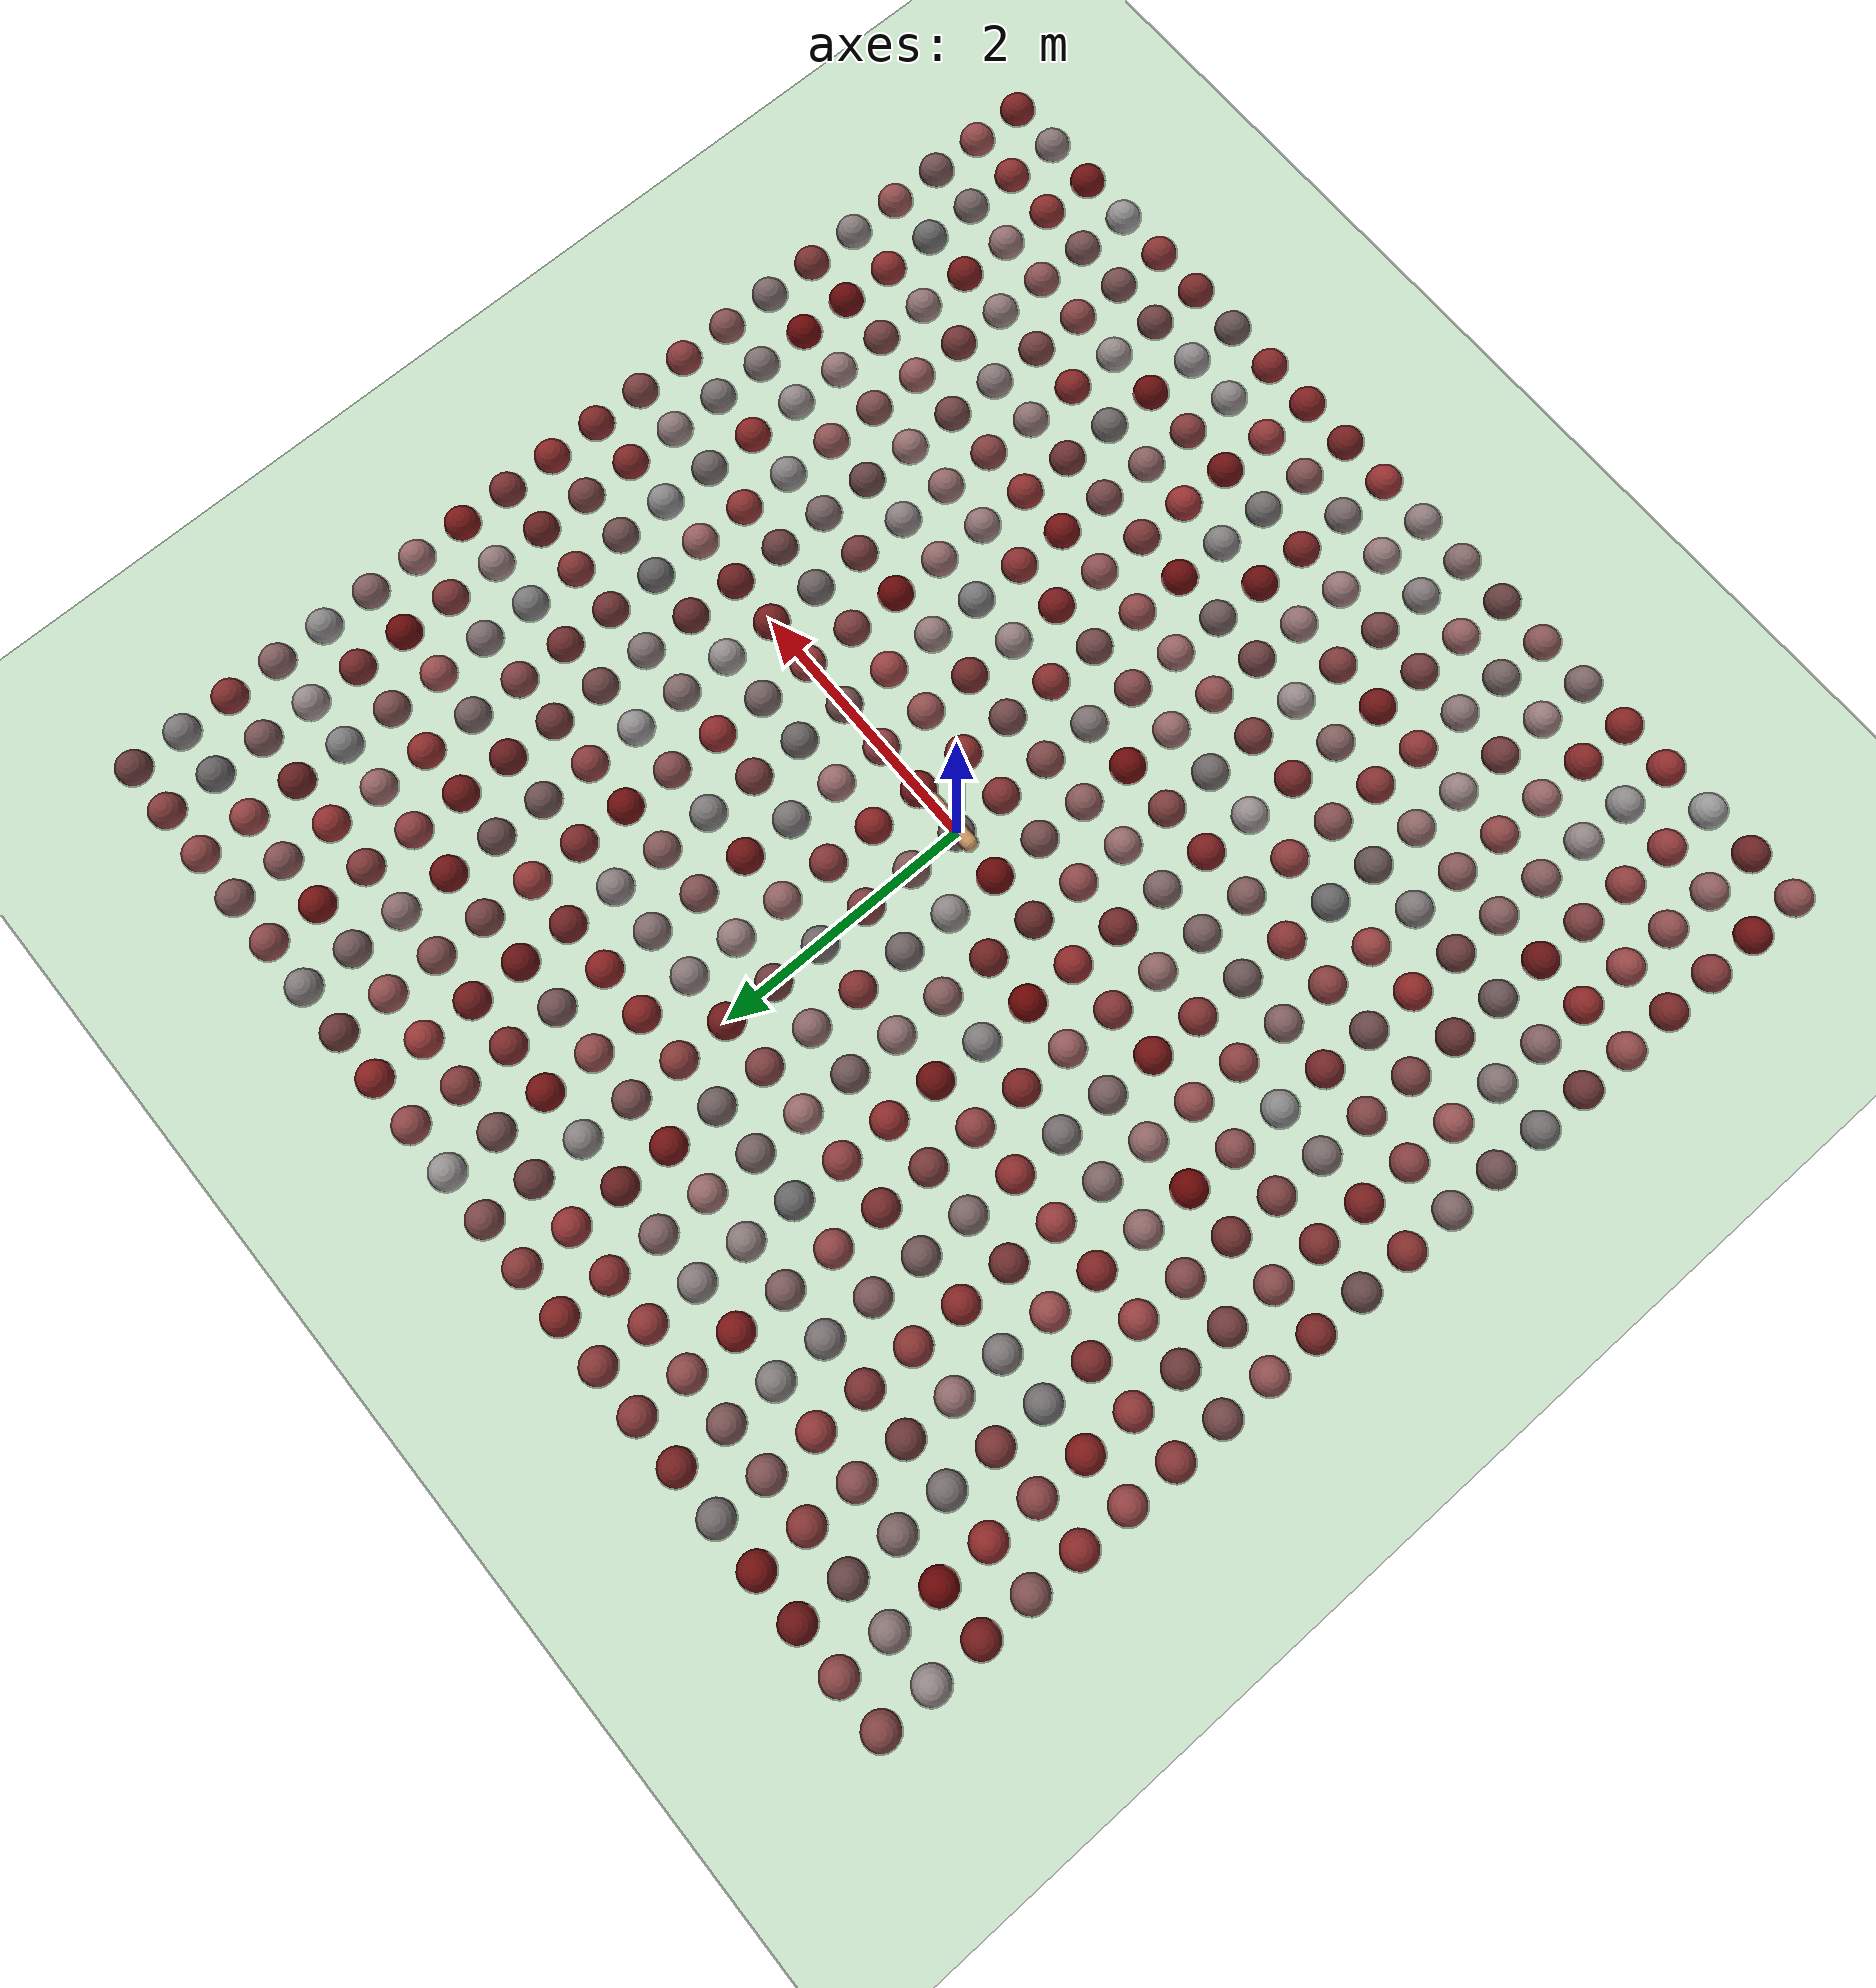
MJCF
<mujoco model="hopper">
  <compiler angle="degree" inertiafromgeom="true"/>
  <default>
    <joint armature="1" damping="1" limited="true"/>
    <geom conaffinity="1" condim="1" contype="1" margin="0.001" material="geom" rgba="0.8 0.6 .4 1" solimp=".8 .8 .01" solref=".02 1"/>
    <motor ctrllimited="true" ctrlrange="-.4 .4"/>
  </default>
  <option integrator="RK4" timestep="0.002"/>
  <visual>
    <map znear="0.02"/>
  </visual>
  <worldbody>
    <light pos="0 0 .6"/>
    <camera name="closeup" pos="0 -4 2" xyaxes="1 0 0 0 1 2"/>
     <!-- Start  sq size 4, spacing 0.4, balls 1,3-->
    <geom name="green_sphere_0_0" pos="0.0 0.0 0.001" size=".13" rgba="0.4680505410427156 0.4034296728520396 0.4034296728520396 1.0"/>
<geom name="green_sphere_0_1" pos="0.0 0.4 0.001" size=".13" rgba="0.5105499601805111 0.354639416788994 0.354639416788994 1.0"/>
<geom name="green_sphere_0_-1" pos="0.0 -0.4 0.001" size=".13" rgba="0.5046903965514052 0.18815869144165676 0.18815869144165676 1.0"/>
<geom name="green_sphere_0_2" pos="0.0 0.8 0.001" size=".13" rgba="0.4967985833634888 0.2463938687618354 0.2463938687618354 1.0"/>
<geom name="green_sphere_0_-2" pos="0.0 -0.8 0.001" size=".13" rgba="0.497772155282503 0.2805601780314163 0.2805601780314163 1.0"/>
<geom name="green_sphere_0_3" pos="0.0 1.2000000000000002 0.001" size=".13" rgba="0.4432379099632507 0.4068937780324804 0.4068937780324804 1.0"/>
<geom name="green_sphere_0_-3" pos="0.0 -1.2000000000000002 0.001" size=".13" rgba="0.48705474198753285 0.44010366828433967 0.44010366828433967 1.0"/>
<geom name="green_sphere_0_4" pos="0.0 1.6 0.001" size=".13" rgba="0.42715481653571014 0.2356029555242013 0.2356029555242013 1.0"/>
<geom name="green_sphere_0_-4" pos="0.0 -1.6 0.001" size=".13" rgba="0.5113062163466534 0.28314888965724794 0.28314888965724794 1.0"/>
<geom name="green_sphere_0_5" pos="0.0 2.0 0.001" size=".13" rgba="0.44028858185463904 0.10080556030725851 0.10080556030725851 1.0"/>
<geom name="green_sphere_0_-5" pos="0.0 -2.0 0.001" size=".13" rgba="0.5894798258602211 0.39124318802759894 0.39124318802759894 1.0"/>
<geom name="green_sphere_0_6" pos="0.0 2.4000000000000004 0.001" size=".13" rgba="0.5276568598822056 0.22430874779273668 0.22430874779273668 1.0"/>
<geom name="green_sphere_0_-6" pos="0.0 -2.4000000000000004 0.001" size=".13" rgba="0.427104581963064 0.3460215418294641 0.3460215418294641 1.0"/>
<geom name="green_sphere_0_7" pos="0.0 2.8000000000000003 0.001" size=".13" rgba="0.47440500087605325 0.29993127459004815 0.29993127459004815 1.0"/>
<geom name="green_sphere_0_-7" pos="0.0 -2.8000000000000003 0.001" size=".13" rgba="0.4037894711102867 0.05478430252653632 0.05478430252653632 1.0"/>
<geom name="green_sphere_0_8" pos="0.0 3.2 0.001" size=".13" rgba="0.533110230436668 0.506194418492692 0.506194418492692 1.0"/>
<geom name="green_sphere_0_-8" pos="0.0 -3.2 0.001" size=".13" rgba="0.4744718117083516 0.12904281284416935 0.12904281284416935 1.0"/>
<geom name="green_sphere_0_9" pos="0.0 3.6 0.001" size=".13" rgba="0.41209825845617026 0.23248889047065566 0.23248889047065566 1.0"/>
<geom name="green_sphere_0_-9" pos="0.0 -3.6 0.001" size=".13" rgba="0.4844265765234975 0.41970326215531223 0.41970326215531223 1.0"/>
<geom name="green_sphere_0_10" pos="0.0 4.0 0.001" size=".13" rgba="0.4844823882913528 0.27754992435599385 0.27754992435599385 1.0"/>
<geom name="green_sphere_0_-10" pos="0.0 -4.0 0.001" size=".13" rgba="0.5855399040026616 0.18982673135086858 0.18982673135086858 1.0"/>
<geom name="green_sphere_1_0" pos="0.4 0.0 0.001" size=".13" rgba="0.48037568919338686 0.10097174915225088 0.10097174915225088 1.0"/>
<geom name="green_sphere_-1_0" pos="-0.4 0.0 0.001" size=".13" rgba="0.4106091059558412 0.03996776814581854 0.03996776814581854 1.0"/>
<geom name="green_sphere_1_1" pos="0.4 0.4 0.001" size=".13" rgba="0.5249579219724203 0.14032794781092572 0.14032794781092572 1.0"/>
<geom name="green_sphere_-1_1" pos="-0.4 0.4 0.001" size=".13" rgba="0.548936707909254 0.521135256995545 0.521135256995545 1.0"/>
<geom name="green_sphere_1_-1" pos="0.4 -0.4 0.001" size=".13" rgba="0.5396665087506514 0.1750551008082215 0.1750551008082215 1.0"/>
<geom name="green_sphere_-1_-1" pos="-0.4 -0.4 0.001" size=".13" rgba="0.4639667598547806 0.2986747896944011 0.2986747896944011 1.0"/>
<geom name="green_sphere_1_2" pos="0.4 0.8 0.001" size=".13" rgba="0.5127785135302106 0.2096190310132734 0.2096190310132734 1.0"/>
<geom name="green_sphere_-1_2" pos="-0.4 0.8 0.001" size=".13" rgba="0.4355640519025791 0.3819373352912954 0.3819373352912954 1.0"/>
<geom name="green_sphere_1_-2" pos="0.4 -0.8 0.001" size=".13" rgba="0.45074256895292275 0.2819398350022588 0.2819398350022588 1.0"/>
<geom name="green_sphere_-1_-2" pos="-0.4 -0.8 0.001" size=".13" rgba="0.5324631011336249 0.34429938515281644 0.34429938515281644 1.0"/>
<geom name="green_sphere_1_3" pos="0.4 1.2000000000000002 0.001" size=".13" rgba="0.5724223980719733 0.38325661912849457 0.38325661912849457 1.0"/>
<geom name="green_sphere_-1_3" pos="-0.4 1.2000000000000002 0.001" size=".13" rgba="0.5138450847287824 0.19008116955504128 0.19008116955504128 1.0"/>
<geom name="green_sphere_1_-3" pos="0.4 -1.2000000000000002 0.001" size=".13" rgba="0.5273469434252612 0.17782037704452636 0.17782037704452636 1.0"/>
<geom name="green_sphere_-1_-3" pos="-0.4 -1.2000000000000002 0.001" size=".13" rgba="0.4255195962069604 0.04541869511812946 0.04541869511812946 1.0"/>
<geom name="green_sphere_1_4" pos="0.4 1.6 0.001" size=".13" rgba="0.5895652122981232 0.48341873670168173 0.48341873670168173 1.0"/>
<geom name="green_sphere_-1_4" pos="-0.4 1.6 0.001" size=".13" rgba="0.5474313768934624 0.40208383255424596 0.40208383255424596 1.0"/>
<geom name="green_sphere_1_-4" pos="0.4 -1.6 0.001" size=".13" rgba="0.44886973156392723 0.27924906755898504 0.27924906755898504 1.0"/>
<geom name="green_sphere_-1_-4" pos="-0.4 -1.6 0.001" size=".13" rgba="0.5793535794793434 0.40870508357960084 0.40870508357960084 1.0"/>
<geom name="green_sphere_1_5" pos="0.4 2.0 0.001" size=".13" rgba="0.5323981326801814 0.47009617263114556 0.47009617263114556 1.0"/>
<geom name="green_sphere_-1_5" pos="-0.4 2.0 0.001" size=".13" rgba="0.49597503703721457 0.25178702244114504 0.25178702244114504 1.0"/>
<geom name="green_sphere_1_-5" pos="0.4 -2.0 0.001" size=".13" rgba="0.5560595522262655 0.2847744721617667 0.2847744721617667 1.0"/>
<geom name="green_sphere_-1_-5" pos="-0.4 -2.0 0.001" size=".13" rgba="0.558374637976701 0.30402035918518944 0.30402035918518944 1.0"/>
<geom name="green_sphere_1_6" pos="0.4 2.4000000000000004 0.001" size=".13" rgba="0.5192893071875383 0.13371299219413035 0.13371299219413035 1.0"/>
<geom name="green_sphere_-1_6" pos="-0.4 2.4000000000000004 0.001" size=".13" rgba="0.43768322100637286 0.3696815103625422 0.3696815103625422 1.0"/>
<geom name="green_sphere_1_-6" pos="0.4 -2.4000000000000004 0.001" size=".13" rgba="0.41597914544311954 0.04433754756269093 0.04433754756269093 1.0"/>
<geom name="green_sphere_-1_-6" pos="-0.4 -2.4000000000000004 0.001" size=".13" rgba="0.4268520811852775 0.24890871382601365 0.24890871382601365 1.0"/>
<geom name="green_sphere_1_7" pos="0.4 2.8000000000000003 0.001" size=".13" rgba="0.5666021343859963 0.28441877201330745 0.28441877201330745 1.0"/>
<geom name="green_sphere_-1_7" pos="-0.4 2.8000000000000003 0.001" size=".13" rgba="0.4457675028579905 0.07005871497343913 0.07005871497343913 1.0"/>
<geom name="green_sphere_1_-7" pos="0.4 -2.8000000000000003 0.001" size=".13" rgba="0.508061807065673 0.49338212916300717 0.49338212916300717 1.0"/>
<geom name="green_sphere_-1_-7" pos="-0.4 -2.8000000000000003 0.001" size=".13" rgba="0.5671951315956203 0.43183106333223237 0.43183106333223237 1.0"/>
<geom name="green_sphere_1_8" pos="0.4 3.2 0.001" size=".13" rgba="0.4489012398275367 0.07178300844328656 0.07178300844328656 1.0"/>
<geom name="green_sphere_-1_8" pos="-0.4 3.2 0.001" size=".13" rgba="0.40439700591728195 0.12222932014755222 0.12222932014755222 1.0"/>
<geom name="green_sphere_1_-8" pos="0.4 -3.2 0.001" size=".13" rgba="0.4448902563630763 0.4279056969287632 0.4279056969287632 1.0"/>
<geom name="green_sphere_-1_-8" pos="-0.4 -3.2 0.001" size=".13" rgba="0.590852740687632 0.45548578271936335 0.45548578271936335 1.0"/>
<geom name="green_sphere_1_9" pos="0.4 3.6 0.001" size=".13" rgba="0.44779782770941184 0.3016126722545286 0.3016126722545286 1.0"/>
<geom name="green_sphere_-1_9" pos="-0.4 3.6 0.001" size=".13" rgba="0.5743182492502807 0.1968422498356442 0.1968422498356442 1.0"/>
<geom name="green_sphere_1_-9" pos="0.4 -3.6 0.001" size=".13" rgba="0.523141939444337 0.3239213286605642 0.3239213286605642 1.0"/>
<geom name="green_sphere_-1_-9" pos="-0.4 -3.6 0.001" size=".13" rgba="0.5916339553000294 0.47856552372812816 0.47856552372812816 1.0"/>
<geom name="green_sphere_1_10" pos="0.4 4.0 0.001" size=".13" rgba="0.5869444361780792 0.5723068650970595 0.5723068650970595 1.0"/>
<geom name="green_sphere_-1_10" pos="-0.4 4.0 0.001" size=".13" rgba="0.5283257381639499 0.21967131532756268 0.21967131532756268 1.0"/>
<geom name="green_sphere_1_-10" pos="0.4 -4.0 0.001" size=".13" rgba="0.45030376717522996 0.12343807204498675 0.12343807204498675 1.0"/>
<geom name="green_sphere_-1_-10" pos="-0.4 -4.0 0.001" size=".13" rgba="0.563448360804282 0.49091323746317994 0.49091323746317994 1.0"/>
<geom name="green_sphere_2_0" pos="0.8 0.0 0.001" size=".13" rgba="0.5715895596332786 0.24796277453810062 0.24796277453810062 1.0"/>
<geom name="green_sphere_-2_0" pos="-0.8 0.0 0.001" size=".13" rgba="0.41222743499274844 0.16543607182464096 0.16543607182464096 1.0"/>
<geom name="green_sphere_2_1" pos="0.8 0.4 0.001" size=".13" rgba="0.5986260900850855 0.41732464215318665 0.41732464215318665 1.0"/>
<geom name="green_sphere_-2_1" pos="-0.8 0.4 0.001" size=".13" rgba="0.4431518127549741 0.13147980646027374 0.13147980646027374 1.0"/>
<geom name="green_sphere_2_-1" pos="0.8 -0.4 0.001" size=".13" rgba="0.5686185101950039 0.3086060823039684 0.3086060823039684 1.0"/>
<geom name="green_sphere_-2_-1" pos="-0.8 -0.4 0.001" size=".13" rgba="0.5564826655804729 0.2826944351898281 0.2826944351898281 1.0"/>
<geom name="green_sphere_2_2" pos="0.8 0.8 0.001" size=".13" rgba="0.4678212433850668 0.4520126850295833 0.4520126850295833 1.0"/>
<geom name="green_sphere_-2_2" pos="-0.8 0.8 0.001" size=".13" rgba="0.5222941214394665 0.3598532042381576 0.3598532042381576 1.0"/>
<geom name="green_sphere_2_-2" pos="0.8 -0.8 0.001" size=".13" rgba="0.4541849084273235 0.16392951957342738 0.16392951957342738 1.0"/>
<geom name="green_sphere_-2_-2" pos="-0.8 -0.8 0.001" size=".13" rgba="0.582440017660965 0.4093485219273018 0.4093485219273018 1.0"/>
<geom name="green_sphere_2_3" pos="0.8 1.2000000000000002 0.001" size=".13" rgba="0.4383514632994071 0.07838836684075534 0.07838836684075534 1.0"/>
<geom name="green_sphere_-2_3" pos="-0.8 1.2000000000000002 0.001" size=".13" rgba="0.560898497517207 0.4377934049362867 0.4377934049362867 1.0"/>
<geom name="green_sphere_2_-3" pos="0.8 -1.2000000000000002 0.001" size=".13" rgba="0.5782654364380474 0.49111652086028124 0.49111652086028124 1.0"/>
<geom name="green_sphere_-2_-3" pos="-0.8 -1.2000000000000002 0.001" size=".13" rgba="0.48425010887396586 0.23324385316792906 0.23324385316792906 1.0"/>
<geom name="green_sphere_2_4" pos="0.8 1.6 0.001" size=".13" rgba="0.5009888096613444 0.3113808703487342 0.3113808703487342 1.0"/>
<geom name="green_sphere_-2_4" pos="-0.8 1.6 0.001" size=".13" rgba="0.4344589140495586 0.3321617081063561 0.3321617081063561 1.0"/>
<geom name="green_sphere_2_-4" pos="0.8 -1.6 0.001" size=".13" rgba="0.47129805656818985 0.09608899445876457 0.09608899445876457 1.0"/>
<geom name="green_sphere_-2_-4" pos="-0.8 -1.6 0.001" size=".13" rgba="0.42961932146104 0.40399460931940184 0.40399460931940184 1.0"/>
<geom name="green_sphere_2_5" pos="0.8 2.0 0.001" size=".13" rgba="0.5047146709517464 0.42232421364730094 0.42232421364730094 1.0"/>
<geom name="green_sphere_-2_5" pos="-0.8 2.0 0.001" size=".13" rgba="0.5962571020017932 0.41425528978792037 0.41425528978792037 1.0"/>
<geom name="green_sphere_2_-5" pos="0.8 -2.0 0.001" size=".13" rgba="0.5535170078342978 0.31727436229526584 0.31727436229526584 1.0"/>
<geom name="green_sphere_-2_-5" pos="-0.8 -2.0 0.001" size=".13" rgba="0.46511377773272455 0.2184249938794385 0.2184249938794385 1.0"/>
<geom name="green_sphere_2_6" pos="0.8 2.4000000000000004 0.001" size=".13" rgba="0.5304091289348423 0.13190318020091574 0.13190318020091574 1.0"/>
<geom name="green_sphere_-2_6" pos="-0.8 2.4000000000000004 0.001" size=".13" rgba="0.4607809498186518 0.3778696927306193 0.3778696927306193 1.0"/>
<geom name="green_sphere_2_-6" pos="0.8 -2.4000000000000004 0.001" size=".13" rgba="0.48819824326570227 0.21750644915936052 0.21750644915936052 1.0"/>
<geom name="green_sphere_-2_-6" pos="-0.8 -2.4000000000000004 0.001" size=".13" rgba="0.5957547343270332 0.537283500216101 0.537283500216101 1.0"/>
<geom name="green_sphere_2_7" pos="0.8 2.8000000000000003 0.001" size=".13" rgba="0.44407859295219043 0.3212905539050328 0.3212905539050328 1.0"/>
<geom name="green_sphere_-2_7" pos="-0.8 2.8000000000000003 0.001" size=".13" rgba="0.5904580535688524 0.4115035739871432 0.4115035739871432 1.0"/>
<geom name="green_sphere_2_-7" pos="0.8 -2.8000000000000003 0.001" size=".13" rgba="0.5933867451453159 0.19496464210471265 0.19496464210471265 1.0"/>
<geom name="green_sphere_-2_-7" pos="-0.8 -2.8000000000000003 0.001" size=".13" rgba="0.49115839298712116 0.22603828084153665 0.22603828084153665 1.0"/>
<geom name="green_sphere_2_8" pos="0.8 3.2 0.001" size=".13" rgba="0.4890809938871564 0.16494931835174748 0.16494931835174748 1.0"/>
<geom name="green_sphere_-2_8" pos="-0.8 3.2 0.001" size=".13" rgba="0.5006418525837544 0.3865619376596897 0.3865619376596897 1.0"/>
<geom name="green_sphere_2_-8" pos="0.8 -3.2 0.001" size=".13" rgba="0.4207702808583733 0.06641916760998934 0.06641916760998934 1.0"/>
<geom name="green_sphere_-2_-8" pos="-0.8 -3.2 0.001" size=".13" rgba="0.455445082552158 0.26517519762577424 0.26517519762577424 1.0"/>
<geom name="green_sphere_2_9" pos="0.8 3.6 0.001" size=".13" rgba="0.5033755606510817 0.22958418920685647 0.22958418920685647 1.0"/>
<geom name="green_sphere_-2_9" pos="-0.8 3.6 0.001" size=".13" rgba="0.5258344469643268 0.1761308624264909 0.1761308624264909 1.0"/>
<geom name="green_sphere_2_-9" pos="0.8 -3.6 0.001" size=".13" rgba="0.5693993905279794 0.21824253667367044 0.21824253667367044 1.0"/>
<geom name="green_sphere_-2_-9" pos="-0.8 -3.6 0.001" size=".13" rgba="0.5139837549720275 0.4772095916175325 0.4772095916175325 1.0"/>
<geom name="green_sphere_2_10" pos="0.8 4.0 0.001" size=".13" rgba="0.5575240654307012 0.27864379268610234 0.27864379268610234 1.0"/>
<geom name="green_sphere_-2_10" pos="-0.8 4.0 0.001" size=".13" rgba="0.5076515456153642 0.13872378065026136 0.13872378065026136 1.0"/>
<geom name="green_sphere_2_-10" pos="0.8 -4.0 0.001" size=".13" rgba="0.49700559854905496 0.12420268550700936 0.12420268550700936 1.0"/>
<geom name="green_sphere_-2_-10" pos="-0.8 -4.0 0.001" size=".13" rgba="0.531070304802941 0.4222412178005732 0.4222412178005732 1.0"/>
<geom name="green_sphere_3_0" pos="1.2000000000000002 0.0 0.001" size=".13" rgba="0.46649432295076854 0.31378556618724546 0.31378556618724546 1.0"/>
<geom name="green_sphere_-3_0" pos="-1.2000000000000002 0.0 0.001" size=".13" rgba="0.5504111182864467 0.16522776518888527 0.16522776518888527 1.0"/>
<geom name="green_sphere_3_1" pos="1.2000000000000002 0.4 0.001" size=".13" rgba="0.41951718754932754 0.385987599721357 0.385987599721357 1.0"/>
<geom name="green_sphere_-3_1" pos="-1.2000000000000002 0.4 0.001" size=".13" rgba="0.41996740866246585 0.022161550036588817 0.022161550036588817 1.0"/>
<geom name="green_sphere_3_-1" pos="1.2000000000000002 -0.4 0.001" size=".13" rgba="0.5956645060092048 0.25666961433846286 0.25666961433846286 1.0"/>
<geom name="green_sphere_-3_-1" pos="-1.2000000000000002 -0.4 0.001" size=".13" rgba="0.44414109484365266 0.1614449169146419 0.1614449169146419 1.0"/>
<geom name="green_sphere_3_2" pos="1.2000000000000002 0.8 0.001" size=".13" rgba="0.46436323103094546 0.22621174797178006 0.22621174797178006 1.0"/>
<geom name="green_sphere_-3_2" pos="-1.2000000000000002 0.8 0.001" size=".13" rgba="0.49214773728062966 0.4801592166680577 0.4801592166680577 1.0"/>
<geom name="green_sphere_3_-2" pos="1.2000000000000002 -0.8 0.001" size=".13" rgba="0.5783510912866427 0.47238876496318044 0.47238876496318044 1.0"/>
<geom name="green_sphere_-3_-2" pos="-1.2000000000000002 -0.8 0.001" size=".13" rgba="0.48395259882429253 0.38238729504134505 0.38238729504134505 1.0"/>
<geom name="green_sphere_3_3" pos="1.2000000000000002 1.2000000000000002 0.001" size=".13" rgba="0.4890912977297759 0.4723603201666257 0.4723603201666257 1.0"/>
<geom name="green_sphere_-3_3" pos="-1.2000000000000002 1.2000000000000002 0.001" size=".13" rgba="0.4128612189753905 0.05792978938913984 0.05792978938913984 1.0"/>
<geom name="green_sphere_3_-3" pos="1.2000000000000002 -1.2000000000000002 0.001" size=".13" rgba="0.468314074048175 0.4595476874144647 0.4595476874144647 1.0"/>
<geom name="green_sphere_-3_-3" pos="-1.2000000000000002 -1.2000000000000002 0.001" size=".13" rgba="0.48495444042926195 0.1142298114841484 0.1142298114841484 1.0"/>
<geom name="green_sphere_3_4" pos="1.2000000000000002 1.6 0.001" size=".13" rgba="0.5197631284046222 0.34906545119359655 0.34906545119359655 1.0"/>
<geom name="green_sphere_-3_4" pos="-1.2000000000000002 1.6 0.001" size=".13" rgba="0.551238199107463 0.16984707993268644 0.16984707993268644 1.0"/>
<geom name="green_sphere_3_-4" pos="1.2000000000000002 -1.6 0.001" size=".13" rgba="0.5349651834407712 0.18035238554296695 0.18035238554296695 1.0"/>
<geom name="green_sphere_-3_-4" pos="-1.2000000000000002 -1.6 0.001" size=".13" rgba="0.5961310247035719 0.5558060138285037 0.5558060138285037 1.0"/>
<geom name="green_sphere_3_5" pos="1.2000000000000002 2.0 0.001" size=".13" rgba="0.5394245762278876 0.48804322770559166 0.48804322770559166 1.0"/>
<geom name="green_sphere_-3_5" pos="-1.2000000000000002 2.0 0.001" size=".13" rgba="0.5503909999211292 0.2362826282945596 0.2362826282945596 1.0"/>
<geom name="green_sphere_3_-5" pos="1.2000000000000002 -2.0 0.001" size=".13" rgba="0.4580425326420356 0.0740408650940374 0.0740408650940374 1.0"/>
<geom name="green_sphere_-3_-5" pos="-1.2000000000000002 -2.0 0.001" size=".13" rgba="0.4763881552642697 0.15626172481542694 0.15626172481542694 1.0"/>
<geom name="green_sphere_3_6" pos="1.2000000000000002 2.4000000000000004 0.001" size=".13" rgba="0.43856990787000877 0.13150208503047522 0.13150208503047522 1.0"/>
<geom name="green_sphere_-3_6" pos="-1.2000000000000002 2.4000000000000004 0.001" size=".13" rgba="0.40388993515233995 0.4002448502897439 0.4002448502897439 1.0"/>
<geom name="green_sphere_3_-6" pos="1.2000000000000002 -2.4000000000000004 0.001" size=".13" rgba="0.464164742246222 0.27760106460854317 0.27760106460854317 1.0"/>
<geom name="green_sphere_-3_-6" pos="-1.2000000000000002 -2.4000000000000004 0.001" size=".13" rgba="0.5117290848029531 0.3703814396104588 0.3703814396104588 1.0"/>
<geom name="green_sphere_3_7" pos="1.2000000000000002 2.8000000000000003 0.001" size=".13" rgba="0.4031334165445321 0.07263017044488784 0.07263017044488784 1.0"/>
<geom name="green_sphere_-3_7" pos="-1.2000000000000002 2.8000000000000003 0.001" size=".13" rgba="0.5389336168574117 0.47342823125023187 0.47342823125023187 1.0"/>
<geom name="green_sphere_3_-7" pos="1.2000000000000002 -2.8000000000000003 0.001" size=".13" rgba="0.5352569077984308 0.37343616908368304 0.37343616908368304 1.0"/>
<geom name="green_sphere_-3_-7" pos="-1.2000000000000002 -2.8000000000000003 0.001" size=".13" rgba="0.43555180574181207 0.0828023394543741 0.0828023394543741 1.0"/>
<geom name="green_sphere_3_8" pos="1.2000000000000002 3.2 0.001" size=".13" rgba="0.4423299078594796 0.10455511550367308 0.10455511550367308 1.0"/>
<geom name="green_sphere_-3_8" pos="-1.2000000000000002 3.2 0.001" size=".13" rgba="0.5160126733931533 0.47413349775019403 0.47413349775019403 1.0"/>
<geom name="green_sphere_3_-8" pos="1.2000000000000002 -3.2 0.001" size=".13" rgba="0.5080395570605601 0.2281046885925797 0.2281046885925797 1.0"/>
<geom name="green_sphere_-3_-8" pos="-1.2000000000000002 -3.2 0.001" size=".13" rgba="0.4528913411035754 0.23836305411252776 0.23836305411252776 1.0"/>
<geom name="green_sphere_3_9" pos="1.2000000000000002 3.6 0.001" size=".13" rgba="0.5967582418681051 0.21753053265673739 0.21753053265673739 1.0"/>
<geom name="green_sphere_-3_9" pos="-1.2000000000000002 3.6 0.001" size=".13" rgba="0.5488869352696786 0.20179061784488644 0.20179061784488644 1.0"/>
<geom name="green_sphere_3_-9" pos="1.2000000000000002 -3.6 0.001" size=".13" rgba="0.5598648045187129 0.536648793896928 0.536648793896928 1.0"/>
<geom name="green_sphere_-3_-9" pos="-1.2000000000000002 -3.6 0.001" size=".13" rgba="0.5771135985867346 0.3723999191579582 0.3723999191579582 1.0"/>
<geom name="green_sphere_3_10" pos="1.2000000000000002 4.0 0.001" size=".13" rgba="0.5256401384235934 0.12600495972503833 0.12600495972503833 1.0"/>
<geom name="green_sphere_-3_10" pos="-1.2000000000000002 4.0 0.001" size=".13" rgba="0.5245250570143928 0.21414386346135583 0.21414386346135583 1.0"/>
<geom name="green_sphere_3_-10" pos="1.2000000000000002 -4.0 0.001" size=".13" rgba="0.519593506982543 0.15051716649163155 0.15051716649163155 1.0"/>
<geom name="green_sphere_-3_-10" pos="-1.2000000000000002 -4.0 0.001" size=".13" rgba="0.40394507161227833 0.24834836616573985 0.24834836616573985 1.0"/>
<geom name="green_sphere_4_0" pos="1.6 0.0 0.001" size=".13" rgba="0.5890999894365685 0.22339967838937946 0.22339967838937946 1.0"/>
<geom name="green_sphere_-4_0" pos="-1.6 0.0 0.001" size=".13" rgba="0.5124860776262405 0.20296108066485874 0.20296108066485874 1.0"/>
<geom name="green_sphere_4_1" pos="1.6 0.4 0.001" size=".13" rgba="0.45530783899464883 0.3858333536262683 0.3858333536262683 1.0"/>
<geom name="green_sphere_-4_1" pos="-1.6 0.4 0.001" size=".13" rgba="0.576580092588159 0.351591878479372 0.351591878479372 1.0"/>
<geom name="green_sphere_4_-1" pos="1.6 -0.4 0.001" size=".13" rgba="0.49291483590908985 0.23681154964312767 0.23681154964312767 1.0"/>
<geom name="green_sphere_-4_-1" pos="-1.6 -0.4 0.001" size=".13" rgba="0.5553009312713213 0.3985864102685026 0.3985864102685026 1.0"/>
<geom name="green_sphere_4_2" pos="1.6 0.8 0.001" size=".13" rgba="0.5555798888474588 0.16949061470910298 0.16949061470910298 1.0"/>
<geom name="green_sphere_-4_2" pos="-1.6 0.8 0.001" size=".13" rgba="0.48662216617428705 0.13732861100192728 0.13732861100192728 1.0"/>
<geom name="green_sphere_4_-2" pos="1.6 -0.8 0.001" size=".13" rgba="0.41490583823476834 0.035369871840707445 0.035369871840707445 1.0"/>
<geom name="green_sphere_-4_-2" pos="-1.6 -0.8 0.001" size=".13" rgba="0.464924542633263 0.3614376289606742 0.3614376289606742 1.0"/>
<geom name="green_sphere_4_3" pos="1.6 1.2000000000000002 0.001" size=".13" rgba="0.5200015179250415 0.29359820090246624 0.29359820090246624 1.0"/>
<geom name="green_sphere_-4_3" pos="-1.6 1.2000000000000002 0.001" size=".13" rgba="0.5537532714182243 0.25215373281805425 0.25215373281805425 1.0"/>
<geom name="green_sphere_4_-3" pos="1.6 -1.2000000000000002 0.001" size=".13" rgba="0.5749396744118054 0.41177242446875434 0.41177242446875434 1.0"/>
<geom name="green_sphere_-4_-3" pos="-1.6 -1.2000000000000002 0.001" size=".13" rgba="0.49625203560615594 0.35187151164736247 0.35187151164736247 1.0"/>
<geom name="green_sphere_4_4" pos="1.6 1.6 0.001" size=".13" rgba="0.42632371382091583 0.06094016232026661 0.06094016232026661 1.0"/>
<geom name="green_sphere_-4_4" pos="-1.6 1.6 0.001" size=".13" rgba="0.47184439688520846 0.21983056396034162 0.21983056396034162 1.0"/>
<geom name="green_sphere_4_-4" pos="1.6 -1.6 0.001" size=".13" rgba="0.5692168669460675 0.4531720620871972 0.4531720620871972 1.0"/>
<geom name="green_sphere_-4_-4" pos="-1.6 -1.6 0.001" size=".13" rgba="0.5547850721688152 0.22965751551336955 0.22965751551336955 1.0"/>
<geom name="green_sphere_4_5" pos="1.6 2.0 0.001" size=".13" rgba="0.47601782512043667 0.16272680565296976 0.16272680565296976 1.0"/>
<geom name="green_sphere_-4_5" pos="-1.6 2.0 0.001" size=".13" rgba="0.4599209325471825 0.1638286409511832 0.1638286409511832 1.0"/>
<geom name="green_sphere_4_-5" pos="1.6 -2.0 0.001" size=".13" rgba="0.545484799436371 0.18167544114071377 0.18167544114071377 1.0"/>
<geom name="green_sphere_-4_-5" pos="-1.6 -2.0 0.001" size=".13" rgba="0.516476359022374 0.312040254595902 0.312040254595902 1.0"/>
<geom name="green_sphere_4_6" pos="1.6 2.4000000000000004 0.001" size=".13" rgba="0.5757729223811188 0.21732581138026458 0.21732581138026458 1.0"/>
<geom name="green_sphere_-4_6" pos="-1.6 2.4000000000000004 0.001" size=".13" rgba="0.5574897669411651 0.2648289700181403 0.2648289700181403 1.0"/>
<geom name="green_sphere_4_-6" pos="1.6 -2.4000000000000004 0.001" size=".13" rgba="0.4337134204633785 0.1941686230861458 0.1941686230861458 1.0"/>
<geom name="green_sphere_-4_-6" pos="-1.6 -2.4000000000000004 0.001" size=".13" rgba="0.5230402254265016 0.1947082914562095 0.1947082914562095 1.0"/>
<geom name="green_sphere_4_7" pos="1.6 2.8000000000000003 0.001" size=".13" rgba="0.45927275338960155 0.25986194395602835 0.25986194395602835 1.0"/>
<geom name="green_sphere_-4_7" pos="-1.6 2.8000000000000003 0.001" size=".13" rgba="0.4811928895247616 0.35554570003674796 0.35554570003674796 1.0"/>
<geom name="green_sphere_4_-7" pos="1.6 -2.8000000000000003 0.001" size=".13" rgba="0.428261259301147 0.402912323892551 0.402912323892551 1.0"/>
<geom name="green_sphere_-4_-7" pos="-1.6 -2.8000000000000003 0.001" size=".13" rgba="0.559152909769749 0.20903093482566165 0.20903093482566165 1.0"/>
<geom name="green_sphere_4_8" pos="1.6 3.2 0.001" size=".13" rgba="0.506310783077877 0.302528607397466 0.302528607397466 1.0"/>
<geom name="green_sphere_-4_8" pos="-1.6 3.2 0.001" size=".13" rgba="0.4867740044445632 0.09151130825795672 0.09151130825795672 1.0"/>
<geom name="green_sphere_4_-8" pos="1.6 -3.2 0.001" size=".13" rgba="0.4094342849863027 0.05078462364872155 0.05078462364872155 1.0"/>
<geom name="green_sphere_-4_-8" pos="-1.6 -3.2 0.001" size=".13" rgba="0.5391843948350149 0.4520087430321297 0.4520087430321297 1.0"/>
<geom name="green_sphere_4_9" pos="1.6 3.6 0.001" size=".13" rgba="0.5687108865862545 0.30789036339768966 0.30789036339768966 1.0"/>
<geom name="green_sphere_-4_9" pos="-1.6 3.6 0.001" size=".13" rgba="0.550294990556947 0.28653617758203753 0.28653617758203753 1.0"/>
<geom name="green_sphere_4_-9" pos="1.6 -3.6 0.001" size=".13" rgba="0.5624754294266344 0.5447884272469087 0.5447884272469087 1.0"/>
<geom name="green_sphere_-4_-9" pos="-1.6 -3.6 0.001" size=".13" rgba="0.45523553069441786 0.38189675014460567 0.38189675014460567 1.0"/>
<geom name="green_sphere_4_10" pos="1.6 4.0 0.001" size=".13" rgba="0.41505972388996604 0.21950595234542536 0.21950595234542536 1.0"/>
<geom name="green_sphere_-4_10" pos="-1.6 4.0 0.001" size=".13" rgba="0.5214553518112972 0.21343283708566113 0.21343283708566113 1.0"/>
<geom name="green_sphere_4_-10" pos="1.6 -4.0 0.001" size=".13" rgba="0.41314152063090903 0.3302972263403229 0.3302972263403229 1.0"/>
<geom name="green_sphere_-4_-10" pos="-1.6 -4.0 0.001" size=".13" rgba="0.5402032219127355 0.33797601972587604 0.33797601972587604 1.0"/>
<geom name="green_sphere_5_0" pos="2.0 0.0 0.001" size=".13" rgba="0.46546844028900936 0.12106204024591266 0.12106204024591266 1.0"/>
<geom name="green_sphere_-5_0" pos="-2.0 0.0 0.001" size=".13" rgba="0.448804982775979 0.06994323115945927 0.06994323115945927 1.0"/>
<geom name="green_sphere_5_1" pos="2.0 0.4 0.001" size=".13" rgba="0.5842240844705971 0.5568412349645504 0.5568412349645504 1.0"/>
<geom name="green_sphere_-5_1" pos="-2.0 0.4 0.001" size=".13" rgba="0.4605471701387209 0.3629329281752953 0.3629329281752953 1.0"/>
<geom name="green_sphere_5_-1" pos="2.0 -0.4 0.001" size=".13" rgba="0.43195551513923963 0.3866954841845137 0.3866954841845137 1.0"/>
<geom name="green_sphere_-5_-1" pos="-2.0 -0.4 0.001" size=".13" rgba="0.511654451150792 0.1893467600985569 0.1893467600985569 1.0"/>
<geom name="green_sphere_5_2" pos="2.0 0.8 0.001" size=".13" rgba="0.505371418987388 0.41058594759424905 0.41058594759424905 1.0"/>
<geom name="green_sphere_-5_2" pos="-2.0 0.8 0.001" size=".13" rgba="0.45458470006775026 0.4197041775165969 0.4197041775165969 1.0"/>
<geom name="green_sphere_5_-2" pos="2.0 -0.8 0.001" size=".13" rgba="0.4539804054110462 0.22550175373130324 0.22550175373130324 1.0"/>
<geom name="green_sphere_-5_-2" pos="-2.0 -0.8 0.001" size=".13" rgba="0.41510020832301286 0.33268702253213145 0.33268702253213145 1.0"/>
<geom name="green_sphere_5_3" pos="2.0 1.2000000000000002 0.001" size=".13" rgba="0.5787697160827204 0.569353605901761 0.569353605901761 1.0"/>
<geom name="green_sphere_-5_3" pos="-2.0 1.2000000000000002 0.001" size=".13" rgba="0.5481916961880036 0.1766666309889247 0.1766666309889247 1.0"/>
<geom name="green_sphere_5_-3" pos="2.0 -1.2000000000000002 0.001" size=".13" rgba="0.5468696380251582 0.49982716367593144 0.49982716367593144 1.0"/>
<geom name="green_sphere_-5_-3" pos="-2.0 -1.2000000000000002 0.001" size=".13" rgba="0.5366528145516027 0.20288887641293135 0.20288887641293135 1.0"/>
<geom name="green_sphere_5_4" pos="2.0 1.6 0.001" size=".13" rgba="0.5311279545793491 0.2334062722052106 0.2334062722052106 1.0"/>
<geom name="green_sphere_-5_4" pos="-2.0 1.6 0.001" size=".13" rgba="0.4868932263362793 0.4071725149480402 0.4071725149480402 1.0"/>
<geom name="green_sphere_5_-4" pos="2.0 -1.6 0.001" size=".13" rgba="0.5669582848706392 0.40544891879864897 0.40544891879864897 1.0"/>
<geom name="green_sphere_-5_-4" pos="-2.0 -1.6 0.001" size=".13" rgba="0.40108606758417503 0.39497846017288885 0.39497846017288885 1.0"/>
<geom name="green_sphere_5_5" pos="2.0 2.0 0.001" size=".13" rgba="0.4190954990964882 0.31499441574771414 0.31499441574771414 1.0"/>
<geom name="green_sphere_-5_5" pos="-2.0 2.0 0.001" size=".13" rgba="0.4422509689836652 0.33665517308074633 0.33665517308074633 1.0"/>
<geom name="green_sphere_5_-5" pos="2.0 -2.0 0.001" size=".13" rgba="0.5110856865132897 0.2489768152290378 0.2489768152290378 1.0"/>
<geom name="green_sphere_-5_-5" pos="-2.0 -2.0 0.001" size=".13" rgba="0.40353049430945165 0.32167418627659017 0.32167418627659017 1.0"/>
<geom name="green_sphere_5_6" pos="2.0 2.4000000000000004 0.001" size=".13" rgba="0.4145386070248344 0.29667352105075007 0.29667352105075007 1.0"/>
<geom name="green_sphere_-5_6" pos="-2.0 2.4000000000000004 0.001" size=".13" rgba="0.4784103846215476 0.33637027229242755 0.33637027229242755 1.0"/>
<geom name="green_sphere_5_-6" pos="2.0 -2.4000000000000004 0.001" size=".13" rgba="0.5518731879711783 0.442619944631185 0.442619944631185 1.0"/>
<geom name="green_sphere_-5_-6" pos="-2.0 -2.4000000000000004 0.001" size=".13" rgba="0.5569786233518933 0.404890612868238 0.404890612868238 1.0"/>
<geom name="green_sphere_5_7" pos="2.0 2.8000000000000003 0.001" size=".13" rgba="0.434340815517541 0.07717730871327033 0.07717730871327033 1.0"/>
<geom name="green_sphere_-5_7" pos="-2.0 2.8000000000000003 0.001" size=".13" rgba="0.4737772856926085 0.43991135643110163 0.43991135643110163 1.0"/>
<geom name="green_sphere_5_-7" pos="2.0 -2.8000000000000003 0.001" size=".13" rgba="0.5222562225979729 0.1484423697110347 0.1484423697110347 1.0"/>
<geom name="green_sphere_-5_-7" pos="-2.0 -2.8000000000000003 0.001" size=".13" rgba="0.5874070582642756 0.49848908332000197 0.49848908332000197 1.0"/>
<geom name="green_sphere_5_8" pos="2.0 3.2 0.001" size=".13" rgba="0.5479058491804069 0.43088200233601903 0.43088200233601903 1.0"/>
<geom name="green_sphere_-5_8" pos="-2.0 3.2 0.001" size=".13" rgba="0.5059147657966309 0.4808318939918449 0.4808318939918449 1.0"/>
<geom name="green_sphere_5_-8" pos="2.0 -3.2 0.001" size=".13" rgba="0.584660414119798 0.5371974853064854 0.5371974853064854 1.0"/>
<geom name="green_sphere_-5_-8" pos="-2.0 -3.2 0.001" size=".13" rgba="0.44537155747301466 0.22603116267584727 0.22603116267584727 1.0"/>
<geom name="green_sphere_5_9" pos="2.0 3.6 0.001" size=".13" rgba="0.45540714175474417 0.3542974570616656 0.3542974570616656 1.0"/>
<geom name="green_sphere_-5_9" pos="-2.0 3.6 0.001" size=".13" rgba="0.47678860198656187 0.32491212684905624 0.32491212684905624 1.0"/>
<geom name="green_sphere_5_-9" pos="2.0 -3.6 0.001" size=".13" rgba="0.43656609796806145 0.25504712859252265 0.25504712859252265 1.0"/>
<geom name="green_sphere_-5_-9" pos="-2.0 -3.6 0.001" size=".13" rgba="0.5968539426962763 0.47841242046687754 0.47841242046687754 1.0"/>
<geom name="green_sphere_5_10" pos="2.0 4.0 0.001" size=".13" rgba="0.5097497053210107 0.48296336893470343 0.48296336893470343 1.0"/>
<geom name="green_sphere_-5_10" pos="-2.0 4.0 0.001" size=".13" rgba="0.4586289102774016 0.12400949977227327 0.12400949977227327 1.0"/>
<geom name="green_sphere_5_-10" pos="2.0 -4.0 0.001" size=".13" rgba="0.4766024100627758 0.1644608237735643 0.1644608237735643 1.0"/>
<geom name="green_sphere_-5_-10" pos="-2.0 -4.0 0.001" size=".13" rgba="0.49266898966785133 0.397335412481441 0.397335412481441 1.0"/>
<geom name="green_sphere_6_0" pos="2.4000000000000004 0.0 0.001" size=".13" rgba="0.4203444245645257 0.1257150666238641 0.1257150666238641 1.0"/>
<geom name="green_sphere_-6_0" pos="-2.4000000000000004 0.0 0.001" size=".13" rgba="0.5769054698951102 0.29969956223091127 0.29969956223091127 1.0"/>
<geom name="green_sphere_6_1" pos="2.4000000000000004 0.4 0.001" size=".13" rgba="0.40583246645244775 0.17099855399355918 0.17099855399355918 1.0"/>
<geom name="green_sphere_-6_1" pos="-2.4000000000000004 0.4 0.001" size=".13" rgba="0.5646538625131643 0.4041747895811745 0.4041747895811745 1.0"/>
<geom name="green_sphere_6_-1" pos="2.4000000000000004 -0.4 0.001" size=".13" rgba="0.4188700125148441 0.24522911231428804 0.24522911231428804 1.0"/>
<geom name="green_sphere_-6_-1" pos="-2.4000000000000004 -0.4 0.001" size=".13" rgba="0.5424815626562997 0.2509367036096241 0.2509367036096241 1.0"/>
<geom name="green_sphere_6_2" pos="2.4000000000000004 0.8 0.001" size=".13" rgba="0.514100486570804 0.44904954825732546 0.44904954825732546 1.0"/>
<geom name="green_sphere_-6_2" pos="-2.4000000000000004 0.8 0.001" size=".13" rgba="0.4947895430846176 0.3995846512759747 0.3995846512759747 1.0"/>
<geom name="green_sphere_6_-2" pos="2.4000000000000004 -0.8 0.001" size=".13" rgba="0.478037560556241 0.3978440133935009 0.3978440133935009 1.0"/>
<geom name="green_sphere_-6_-2" pos="-2.4000000000000004 -0.8 0.001" size=".13" rgba="0.4984555402338236 0.3719657651725786 0.3719657651725786 1.0"/>
<geom name="green_sphere_6_3" pos="2.4000000000000004 1.2000000000000002 0.001" size=".13" rgba="0.44473124847702583 0.2730715413388245 0.2730715413388245 1.0"/>
<geom name="green_sphere_-6_3" pos="-2.4000000000000004 1.2000000000000002 0.001" size=".13" rgba="0.5810645587780285 0.22999149938437902 0.22999149938437902 1.0"/>
<geom name="green_sphere_6_-3" pos="2.4000000000000004 -1.2000000000000002 0.001" size=".13" rgba="0.40460637013473044 0.2635335463609251 0.2635335463609251 1.0"/>
<geom name="green_sphere_-6_-3" pos="-2.4000000000000004 -1.2000000000000002 0.001" size=".13" rgba="0.5270953134683195 0.24015527596844993 0.24015527596844993 1.0"/>
<geom name="green_sphere_6_4" pos="2.4000000000000004 1.6 0.001" size=".13" rgba="0.4318473128676993 0.21016442894723927 0.21016442894723927 1.0"/>
<geom name="green_sphere_-6_4" pos="-2.4000000000000004 1.6 0.001" size=".13" rgba="0.4319381154290437 0.1807814244695048 0.1807814244695048 1.0"/>
<geom name="green_sphere_6_-4" pos="2.4000000000000004 -1.6 0.001" size=".13" rgba="0.5967387184117443 0.43938076826219463 0.43938076826219463 1.0"/>
<geom name="green_sphere_-6_-4" pos="-2.4000000000000004 -1.6 0.001" size=".13" rgba="0.5887547496318744 0.2520957040197298 0.2520957040197298 1.0"/>
<geom name="green_sphere_6_5" pos="2.4000000000000004 2.0 0.001" size=".13" rgba="0.40526378443558086 0.11289083995287186 0.11289083995287186 1.0"/>
<geom name="green_sphere_-6_5" pos="-2.4000000000000004 2.0 0.001" size=".13" rgba="0.5195695505774861 0.14770509397532583 0.14770509397532583 1.0"/>
<geom name="green_sphere_6_-5" pos="2.4000000000000004 -2.0 0.001" size=".13" rgba="0.4395397783175747 0.26385332985048665 0.26385332985048665 1.0"/>
<geom name="green_sphere_-6_-5" pos="-2.4000000000000004 -2.0 0.001" size=".13" rgba="0.49440462753825587 0.4690869889311054 0.4690869889311054 1.0"/>
<geom name="green_sphere_6_6" pos="2.4000000000000004 2.4000000000000004 0.001" size=".13" rgba="0.4390568827940472 0.0915250314563586 0.0915250314563586 1.0"/>
<geom name="green_sphere_-6_6" pos="-2.4000000000000004 2.4000000000000004 0.001" size=".13" rgba="0.5353551971576382 0.2035086487687871 0.2035086487687871 1.0"/>
<geom name="green_sphere_6_-6" pos="2.4000000000000004 -2.4000000000000004 0.001" size=".13" rgba="0.5392988546860844 0.4708419619414633 0.4708419619414633 1.0"/>
<geom name="green_sphere_-6_-6" pos="-2.4000000000000004 -2.4000000000000004 0.001" size=".13" rgba="0.5277446816831411 0.3480942879061326 0.3480942879061326 1.0"/>
<geom name="green_sphere_6_7" pos="2.4000000000000004 2.8000000000000003 0.001" size=".13" rgba="0.5579849973372935 0.24380481459765907 0.24380481459765907 1.0"/>
<geom name="green_sphere_-6_7" pos="-2.4000000000000004 2.8000000000000003 0.001" size=".13" rgba="0.4737856478154665 0.18757207385022284 0.18757207385022284 1.0"/>
<geom name="green_sphere_6_-7" pos="2.4000000000000004 -2.8000000000000003 0.001" size=".13" rgba="0.4588815756982323 0.24552828997213438 0.24552828997213438 1.0"/>
<geom name="green_sphere_-6_-7" pos="-2.4000000000000004 -2.8000000000000003 0.001" size=".13" rgba="0.5630640109942829 0.2773709391639016 0.2773709391639016 1.0"/>
<geom name="green_sphere_6_8" pos="2.4000000000000004 3.2 0.001" size=".13" rgba="0.4995487279673579 0.22293903993847264 0.22293903993847264 1.0"/>
<geom name="green_sphere_-6_8" pos="-2.4000000000000004 3.2 0.001" size=".13" rgba="0.5584869867500383 0.2132172015476253 0.2132172015476253 1.0"/>
<geom name="green_sphere_6_-8" pos="2.4000000000000004 -3.2 0.001" size=".13" rgba="0.5352335552768066 0.27041802201401854 0.27041802201401854 1.0"/>
<geom name="green_sphere_-6_-8" pos="-2.4000000000000004 -3.2 0.001" size=".13" rgba="0.5936637757189216 0.3984398128188169 0.3984398128188169 1.0"/>
<geom name="green_sphere_6_9" pos="2.4000000000000004 3.6 0.001" size=".13" rgba="0.4576610082709382 0.07153002871694919 0.07153002871694919 1.0"/>
<geom name="green_sphere_-6_9" pos="-2.4000000000000004 3.6 0.001" size=".13" rgba="0.49034953303607076 0.3174917181488474 0.3174917181488474 1.0"/>
<geom name="green_sphere_6_-9" pos="2.4000000000000004 -3.6 0.001" size=".13" rgba="0.4621570347951677 0.30366068617109165 0.30366068617109165 1.0"/>
<geom name="green_sphere_-6_-9" pos="-2.4000000000000004 -3.6 0.001" size=".13" rgba="0.5178963022522171 0.1491374387754859 0.1491374387754859 1.0"/>
<geom name="green_sphere_6_10" pos="2.4000000000000004 4.0 0.001" size=".13" rgba="0.5411252325755795 0.27686543358363164 0.27686543358363164 1.0"/>
<geom name="green_sphere_-6_10" pos="-2.4000000000000004 4.0 0.001" size=".13" rgba="0.453129656599019 0.41806273818753115 0.41806273818753115 1.0"/>
<geom name="green_sphere_6_-10" pos="2.4000000000000004 -4.0 0.001" size=".13" rgba="0.5320183456402994 0.1932315088555528 0.1932315088555528 1.0"/>
<geom name="green_sphere_-6_-10" pos="-2.4000000000000004 -4.0 0.001" size=".13" rgba="0.5200382768978946 0.14407202647832562 0.14407202647832562 1.0"/>
<geom name="green_sphere_7_0" pos="2.8000000000000003 0.0 0.001" size=".13" rgba="0.5937409103763953 0.3721689791368311 0.3721689791368311 1.0"/>
<geom name="green_sphere_-7_0" pos="-2.8000000000000003 0.0 0.001" size=".13" rgba="0.5310928196957151 0.3011682668378333 0.3011682668378333 1.0"/>
<geom name="green_sphere_7_1" pos="2.8000000000000003 0.4 0.001" size=".13" rgba="0.40103995551814586 0.3898100638475041 0.3898100638475041 1.0"/>
<geom name="green_sphere_-7_1" pos="-2.8000000000000003 0.4 0.001" size=".13" rgba="0.4198504068366409 0.025872042694636166 0.025872042694636166 1.0"/>
<geom name="green_sphere_7_-1" pos="2.8000000000000003 -0.4 0.001" size=".13" rgba="0.5560799817077025 0.18927963046127094 0.18927963046127094 1.0"/>
<geom name="green_sphere_-7_-1" pos="-2.8000000000000003 -0.4 0.001" size=".13" rgba="0.5336001115450338 0.5310901882202969 0.5310901882202969 1.0"/>
<geom name="green_sphere_7_2" pos="2.8000000000000003 0.8 0.001" size=".13" rgba="0.4387542771273709 0.19973662732092662 0.19973662732092662 1.0"/>
<geom name="green_sphere_-7_2" pos="-2.8000000000000003 0.8 0.001" size=".13" rgba="0.5584068858646427 0.4052383526937633 0.4052383526937633 1.0"/>
<geom name="green_sphere_7_-2" pos="2.8000000000000003 -0.8 0.001" size=".13" rgba="0.5320246738506318 0.5175968355143495 0.5175968355143495 1.0"/>
<geom name="green_sphere_-7_-2" pos="-2.8000000000000003 -0.8 0.001" size=".13" rgba="0.4543030863412443 0.1498500186823885 0.1498500186823885 1.0"/>
<geom name="green_sphere_7_3" pos="2.8000000000000003 1.2000000000000002 0.001" size=".13" rgba="0.4406918669020202 0.17962245929729526 0.17962245929729526 1.0"/>
<geom name="green_sphere_-7_3" pos="-2.8000000000000003 1.2000000000000002 0.001" size=".13" rgba="0.49843297803810577 0.13915197054960216 0.13915197054960216 1.0"/>
<geom name="green_sphere_7_-3" pos="2.8000000000000003 -1.2000000000000002 0.001" size=".13" rgba="0.5591950804283111 0.3195683481709282 0.3195683481709282 1.0"/>
<geom name="green_sphere_-7_-3" pos="-2.8000000000000003 -1.2000000000000002 0.001" size=".13" rgba="0.41495188206876704 0.27976516888414904 0.27976516888414904 1.0"/>
<geom name="green_sphere_7_4" pos="2.8000000000000003 1.6 0.001" size=".13" rgba="0.5010700899141345 0.25794756722295914 0.25794756722295914 1.0"/>
<geom name="green_sphere_-7_4" pos="-2.8000000000000003 1.6 0.001" size=".13" rgba="0.5957453426566961 0.28975010492325226 0.28975010492325226 1.0"/>
<geom name="green_sphere_7_-4" pos="2.8000000000000003 -1.6 0.001" size=".13" rgba="0.5112552545633846 0.30591689998348315 0.30591689998348315 1.0"/>
<geom name="green_sphere_-7_-4" pos="-2.8000000000000003 -1.6 0.001" size=".13" rgba="0.5512411855659084 0.15585858843892736 0.15585858843892736 1.0"/>
<geom name="green_sphere_7_5" pos="2.8000000000000003 2.0 0.001" size=".13" rgba="0.4568059805069002 0.3704792209150458 0.3704792209150458 1.0"/>
<geom name="green_sphere_-7_5" pos="-2.8000000000000003 2.0 0.001" size=".13" rgba="0.4839465826986643 0.4584394753477901 0.4584394753477901 1.0"/>
<geom name="green_sphere_7_-5" pos="2.8000000000000003 -2.0 0.001" size=".13" rgba="0.5902704892219295 0.35440590769049485 0.35440590769049485 1.0"/>
<geom name="green_sphere_-7_-5" pos="-2.8000000000000003 -2.0 0.001" size=".13" rgba="0.4174942053748036 0.23083681314106758 0.23083681314106758 1.0"/>
<geom name="green_sphere_7_6" pos="2.8000000000000003 2.4000000000000004 0.001" size=".13" rgba="0.5565257019602288 0.17300900356232934 0.17300900356232934 1.0"/>
<geom name="green_sphere_-7_6" pos="-2.8000000000000003 2.4000000000000004 0.001" size=".13" rgba="0.5624544372977777 0.4156646374173981 0.4156646374173981 1.0"/>
<geom name="green_sphere_7_-6" pos="2.8000000000000003 -2.4000000000000004 0.001" size=".13" rgba="0.44718543808705075 0.20637250500093696 0.20637250500093696 1.0"/>
<geom name="green_sphere_-7_-6" pos="-2.8000000000000003 -2.4000000000000004 0.001" size=".13" rgba="0.5237062117795571 0.3667418878394888 0.3667418878394888 1.0"/>
<geom name="green_sphere_7_7" pos="2.8000000000000003 2.8000000000000003 0.001" size=".13" rgba="0.5871693543941663 0.391875935775864 0.391875935775864 1.0"/>
<geom name="green_sphere_-7_7" pos="-2.8000000000000003 2.8000000000000003 0.001" size=".13" rgba="0.4173498333210832 0.21442006318436102 0.21442006318436102 1.0"/>
<geom name="green_sphere_7_-7" pos="2.8000000000000003 -2.8000000000000003 0.001" size=".13" rgba="0.5644401405274259 0.47290502050808536 0.47290502050808536 1.0"/>
<geom name="green_sphere_-7_-7" pos="-2.8000000000000003 -2.8000000000000003 0.001" size=".13" rgba="0.5286613037622168 0.36473507791465554 0.36473507791465554 1.0"/>
<geom name="green_sphere_7_8" pos="2.8000000000000003 3.2 0.001" size=".13" rgba="0.5708603981925243 0.18327134133850193 0.18327134133850193 1.0"/>
<geom name="green_sphere_-7_8" pos="-2.8000000000000003 3.2 0.001" size=".13" rgba="0.5199926452243032 0.29805807751576086 0.29805807751576086 1.0"/>
<geom name="green_sphere_7_-8" pos="2.8000000000000003 -3.2 0.001" size=".13" rgba="0.553645499611814 0.32656752072923495 0.32656752072923495 1.0"/>
<geom name="green_sphere_-7_-8" pos="-2.8000000000000003 -3.2 0.001" size=".13" rgba="0.56822266305363 0.51752084673761 0.51752084673761 1.0"/>
<geom name="green_sphere_7_9" pos="2.8000000000000003 3.6 0.001" size=".13" rgba="0.5174374865881787 0.3227922537874462 0.3227922537874462 1.0"/>
<geom name="green_sphere_-7_9" pos="-2.8000000000000003 3.6 0.001" size=".13" rgba="0.5191000314590534 0.2035482783276581 0.2035482783276581 1.0"/>
<geom name="green_sphere_7_-9" pos="2.8000000000000003 -3.6 0.001" size=".13" rgba="0.4701714403098183 0.3165435848654652 0.3165435848654652 1.0"/>
<geom name="green_sphere_-7_-9" pos="-2.8000000000000003 -3.6 0.001" size=".13" rgba="0.5502623608681594 0.536721794584328 0.536721794584328 1.0"/>
<geom name="green_sphere_7_10" pos="2.8000000000000003 4.0 0.001" size=".13" rgba="0.4902535298209146 0.3277829553053543 0.3277829553053543 1.0"/>
<geom name="green_sphere_-7_10" pos="-2.8000000000000003 4.0 0.001" size=".13" rgba="0.44309568809169386 0.06056849226069044 0.06056849226069044 1.0"/>
<geom name="green_sphere_7_-10" pos="2.8000000000000003 -4.0 0.001" size=".13" rgba="0.5829165556915858 0.5732385782316702 0.5732385782316702 1.0"/>
<geom name="green_sphere_-7_-10" pos="-2.8000000000000003 -4.0 0.001" size=".13" rgba="0.5644417425775566 0.169659720664754 0.169659720664754 1.0"/>
<geom name="green_sphere_8_0" pos="3.2 0.0 0.001" size=".13" rgba="0.5391517975311566 0.5294906773522984 0.5294906773522984 1.0"/>
<geom name="green_sphere_-8_0" pos="-3.2 0.0 0.001" size=".13" rgba="0.4855951477142769 0.2519397039376937 0.2519397039376937 1.0"/>
<geom name="green_sphere_8_1" pos="3.2 0.4 0.001" size=".13" rgba="0.4414967578838016 0.3147528246349735 0.3147528246349735 1.0"/>
<geom name="green_sphere_-8_1" pos="-3.2 0.4 0.001" size=".13" rgba="0.446657477121874 0.1866360431239053 0.1866360431239053 1.0"/>
<geom name="green_sphere_8_-1" pos="3.2 -0.4 0.001" size=".13" rgba="0.4441981422262158 0.40107190615555033 0.40107190615555033 1.0"/>
<geom name="green_sphere_-8_-1" pos="-3.2 -0.4 0.001" size=".13" rgba="0.4820828354788046 0.41520790532800717 0.41520790532800717 1.0"/>
<geom name="green_sphere_8_2" pos="3.2 0.8 0.001" size=".13" rgba="0.5093093284488558 0.20284501453060222 0.20284501453060222 1.0"/>
<geom name="green_sphere_-8_2" pos="-3.2 0.8 0.001" size=".13" rgba="0.5079067328157659 0.27985853159958696 0.27985853159958696 1.0"/>
<geom name="green_sphere_8_-2" pos="3.2 -0.8 0.001" size=".13" rgba="0.5357446960633462 0.14871745738234432 0.14871745738234432 1.0"/>
<geom name="green_sphere_-8_-2" pos="-3.2 -0.8 0.001" size=".13" rgba="0.5105866619365091 0.2655859217519167 0.2655859217519167 1.0"/>
<geom name="green_sphere_8_3" pos="3.2 1.2000000000000002 0.001" size=".13" rgba="0.4814182691216153 0.4771508090604442 0.4771508090604442 1.0"/>
<geom name="green_sphere_-8_3" pos="-3.2 1.2000000000000002 0.001" size=".13" rgba="0.5808483257726054 0.24578688687275263 0.24578688687275263 1.0"/>
<geom name="green_sphere_8_-3" pos="3.2 -1.2000000000000002 0.001" size=".13" rgba="0.571476886654604 0.5327193575312288 0.5327193575312288 1.0"/>
<geom name="green_sphere_-8_-3" pos="-3.2 -1.2000000000000002 0.001" size=".13" rgba="0.47957100846468576 0.2543504982339819 0.2543504982339819 1.0"/>
<geom name="green_sphere_8_4" pos="3.2 1.6 0.001" size=".13" rgba="0.49451765174651263 0.42698271136082405 0.42698271136082405 1.0"/>
<geom name="green_sphere_-8_4" pos="-3.2 1.6 0.001" size=".13" rgba="0.47181043761520375 0.1576870586460546 0.1576870586460546 1.0"/>
<geom name="green_sphere_8_-4" pos="3.2 -1.6 0.001" size=".13" rgba="0.5917008132130586 0.469455959862792 0.469455959862792 1.0"/>
<geom name="green_sphere_-8_-4" pos="-3.2 -1.6 0.001" size=".13" rgba="0.4002210361458859 0.19775286046464702 0.19775286046464702 1.0"/>
<geom name="green_sphere_8_5" pos="3.2 2.0 0.001" size=".13" rgba="0.5948888390978938 0.30109981024855553 0.30109981024855553 1.0"/>
<geom name="green_sphere_-8_5" pos="-3.2 2.0 0.001" size=".13" rgba="0.44012290888352384 0.4271332874311647 0.4271332874311647 1.0"/>
<geom name="green_sphere_8_-5" pos="3.2 -2.0 0.001" size=".13" rgba="0.4660375631885407 0.2584905519152563 0.2584905519152563 1.0"/>
<geom name="green_sphere_-8_-5" pos="-3.2 -2.0 0.001" size=".13" rgba="0.41175360678721606 0.3243407601808144 0.3243407601808144 1.0"/>
<geom name="green_sphere_8_6" pos="3.2 2.4000000000000004 0.001" size=".13" rgba="0.49047050629045996 0.3048647394300861 0.3048647394300861 1.0"/>
<geom name="green_sphere_-8_6" pos="-3.2 2.4000000000000004 0.001" size=".13" rgba="0.4751079991898427 0.20127786401370734 0.20127786401370734 1.0"/>
<geom name="green_sphere_8_-6" pos="3.2 -2.4000000000000004 0.001" size=".13" rgba="0.571966933411445 0.45314293974205916 0.45314293974205916 1.0"/>
<geom name="green_sphere_-8_-6" pos="-3.2 -2.4000000000000004 0.001" size=".13" rgba="0.40228193205976825 0.07195460139489906 0.07195460139489906 1.0"/>
<geom name="green_sphere_8_7" pos="3.2 2.8000000000000003 0.001" size=".13" rgba="0.493621840668187 0.49086922676564704 0.49086922676564704 1.0"/>
<geom name="green_sphere_-8_7" pos="-3.2 2.8000000000000003 0.001" size=".13" rgba="0.4592958842778691 0.41967178061581445 0.41967178061581445 1.0"/>
<geom name="green_sphere_8_-7" pos="3.2 -2.8000000000000003 0.001" size=".13" rgba="0.46551445146757797 0.10059071680696968 0.10059071680696968 1.0"/>
<geom name="green_sphere_-8_-7" pos="-3.2 -2.8000000000000003 0.001" size=".13" rgba="0.49731433487709475 0.2522792787346839 0.2522792787346839 1.0"/>
<geom name="green_sphere_8_8" pos="3.2 3.2 0.001" size=".13" rgba="0.4074010871249053 0.12820806419825925 0.12820806419825925 1.0"/>
<geom name="green_sphere_-8_8" pos="-3.2 3.2 0.001" size=".13" rgba="0.48461501679379654 0.3868457720288747 0.3868457720288747 1.0"/>
<geom name="green_sphere_8_-8" pos="3.2 -3.2 0.001" size=".13" rgba="0.5840681409200471 0.44141077633209247 0.44141077633209247 1.0"/>
<geom name="green_sphere_-8_-8" pos="-3.2 -3.2 0.001" size=".13" rgba="0.5563827511810604 0.23791472886088816 0.23791472886088816 1.0"/>
<geom name="green_sphere_8_9" pos="3.2 3.6 0.001" size=".13" rgba="0.579142821768852 0.2562853031998743 0.2562853031998743 1.0"/>
<geom name="green_sphere_-8_9" pos="-3.2 3.6 0.001" size=".13" rgba="0.4040789019904435 0.2683792950884461 0.2683792950884461 1.0"/>
<geom name="green_sphere_8_-9" pos="3.2 -3.6 0.001" size=".13" rgba="0.5411251214810011 0.17119799134998404 0.17119799134998404 1.0"/>
<geom name="green_sphere_-8_-9" pos="-3.2 -3.6 0.001" size=".13" rgba="0.563951214656736 0.2176756086756072 0.2176756086756072 1.0"/>
<geom name="green_sphere_8_10" pos="3.2 4.0 0.001" size=".13" rgba="0.5574768754696087 0.27417121800800937 0.27417121800800937 1.0"/>
<geom name="green_sphere_-8_10" pos="-3.2 4.0 0.001" size=".13" rgba="0.4163400611567426 0.0758991312363112 0.0758991312363112 1.0"/>
<geom name="green_sphere_8_-10" pos="3.2 -4.0 0.001" size=".13" rgba="0.43982345401255135 0.07203830486581236 0.07203830486581236 1.0"/>
<geom name="green_sphere_-8_-10" pos="-3.2 -4.0 0.001" size=".13" rgba="0.5928673887583765 0.5883193130220579 0.5883193130220579 1.0"/>
<geom name="green_sphere_9_0" pos="3.6 0.0 0.001" size=".13" rgba="0.5000262296547102 0.14815306229689162 0.14815306229689162 1.0"/>
<geom name="green_sphere_-9_0" pos="-3.6 0.0 0.001" size=".13" rgba="0.4864654221711925 0.17575486219751674 0.17575486219751674 1.0"/>
<geom name="green_sphere_9_1" pos="3.6 0.4 0.001" size=".13" rgba="0.4644656225377365 0.2587816450515113 0.2587816450515113 1.0"/>
<geom name="green_sphere_-9_1" pos="-3.6 0.4 0.001" size=".13" rgba="0.5282541308611568 0.2875213335070772 0.2875213335070772 1.0"/>
<geom name="green_sphere_9_-1" pos="3.6 -0.4 0.001" size=".13" rgba="0.5658820228738756 0.48134849456177276 0.48134849456177276 1.0"/>
<geom name="green_sphere_-9_-1" pos="-3.6 -0.4 0.001" size=".13" rgba="0.469353864160127 0.12253047900211145 0.12253047900211145 1.0"/>
<geom name="green_sphere_9_2" pos="3.6 0.8 0.001" size=".13" rgba="0.4193764392888994 0.1362147430001941 0.1362147430001941 1.0"/>
<geom name="green_sphere_-9_2" pos="-3.6 0.8 0.001" size=".13" rgba="0.4378684304896725 0.22983970499766307 0.22983970499766307 1.0"/>
<geom name="green_sphere_9_-2" pos="3.6 -0.8 0.001" size=".13" rgba="0.4860536104684229 0.4515157160972268 0.4515157160972268 1.0"/>
<geom name="green_sphere_-9_-2" pos="-3.6 -0.8 0.001" size=".13" rgba="0.5260483254735073 0.24919522895240626 0.24919522895240626 1.0"/>
<geom name="green_sphere_9_3" pos="3.6 1.2000000000000002 0.001" size=".13" rgba="0.5791014073135335 0.4796004358899983 0.4796004358899983 1.0"/>
<geom name="green_sphere_-9_3" pos="-3.6 1.2000000000000002 0.001" size=".13" rgba="0.422281339210713 0.22161967183498413 0.22161967183498413 1.0"/>
<geom name="green_sphere_9_-3" pos="3.6 -1.2000000000000002 0.001" size=".13" rgba="0.49842645220139015 0.4373246689339596 0.4373246689339596 1.0"/>
<geom name="green_sphere_-9_-3" pos="-3.6 -1.2000000000000002 0.001" size=".13" rgba="0.5925774509140878 0.3216746923566934 0.3216746923566934 1.0"/>
<geom name="green_sphere_9_4" pos="3.6 1.6 0.001" size=".13" rgba="0.4966374557060848 0.2141132813468341 0.2141132813468341 1.0"/>
<geom name="green_sphere_-9_4" pos="-3.6 1.6 0.001" size=".13" rgba="0.5515040399654906 0.20882018206146458 0.20882018206146458 1.0"/>
<geom name="green_sphere_9_-4" pos="3.6 -1.6 0.001" size=".13" rgba="0.4229838543313953 0.037466622829073704 0.037466622829073704 1.0"/>
<geom name="green_sphere_-9_-4" pos="-3.6 -1.6 0.001" size=".13" rgba="0.5085585769977954 0.44405668195736797 0.44405668195736797 1.0"/>
<geom name="green_sphere_9_5" pos="3.6 2.0 0.001" size=".13" rgba="0.41001207238657517 0.044419714345668604 0.044419714345668604 1.0"/>
<geom name="green_sphere_-9_5" pos="-3.6 2.0 0.001" size=".13" rgba="0.4915258624828664 0.10297518432104175 0.10297518432104175 1.0"/>
<geom name="green_sphere_9_-5" pos="3.6 -2.0 0.001" size=".13" rgba="0.4052681227924533 0.03915616970922198 0.03915616970922198 1.0"/>
<geom name="green_sphere_-9_-5" pos="-3.6 -2.0 0.001" size=".13" rgba="0.5109962539157729 0.38234053892493947 0.38234053892493947 1.0"/>
<geom name="green_sphere_9_6" pos="3.6 2.4000000000000004 0.001" size=".13" rgba="0.46545726708099766 0.16149594243996906 0.16149594243996906 1.0"/>
<geom name="green_sphere_-9_6" pos="-3.6 2.4000000000000004 0.001" size=".13" rgba="0.5355992925319399 0.25947565566961367 0.25947565566961367 1.0"/>
<geom name="green_sphere_9_-6" pos="3.6 -2.4000000000000004 0.001" size=".13" rgba="0.5508636410261225 0.1786632880353735 0.1786632880353735 1.0"/>
<geom name="green_sphere_-9_-6" pos="-3.6 -2.4000000000000004 0.001" size=".13" rgba="0.5418196935577261 0.15359259549415072 0.15359259549415072 1.0"/>
<geom name="green_sphere_9_7" pos="3.6 2.8000000000000003 0.001" size=".13" rgba="0.5882037697829889 0.5337301527330255 0.5337301527330255 1.0"/>
<geom name="green_sphere_-9_7" pos="-3.6 2.8000000000000003 0.001" size=".13" rgba="0.5581593552207765 0.16005576934645493 0.16005576934645493 1.0"/>
<geom name="green_sphere_9_-7" pos="3.6 -2.8000000000000003 0.001" size=".13" rgba="0.41973539017307215 0.41837275818259867 0.41837275818259867 1.0"/>
<geom name="green_sphere_-9_-7" pos="-3.6 -2.8000000000000003 0.001" size=".13" rgba="0.5917820587402702 0.2711641240096783 0.2711641240096783 1.0"/>
<geom name="green_sphere_9_8" pos="3.6 3.2 0.001" size=".13" rgba="0.4758040973914027 0.33281638451539863 0.33281638451539863 1.0"/>
<geom name="green_sphere_-9_8" pos="-3.6 3.2 0.001" size=".13" rgba="0.4140590439509392 0.02646194264116436 0.02646194264116436 1.0"/>
<geom name="green_sphere_9_-8" pos="3.6 -3.2 0.001" size=".13" rgba="0.4800473860059748 0.40746414897949496 0.40746414897949496 1.0"/>
<geom name="green_sphere_-9_-8" pos="-3.6 -3.2 0.001" size=".13" rgba="0.5513533649884399 0.30034352076699555 0.30034352076699555 1.0"/>
<geom name="green_sphere_9_9" pos="3.6 3.6 0.001" size=".13" rgba="0.40336341978628254 0.38914158855574166 0.38914158855574166 1.0"/>
<geom name="green_sphere_-9_9" pos="-3.6 3.6 0.001" size=".13" rgba="0.5352550234917381 0.4502977973375449 0.4502977973375449 1.0"/>
<geom name="green_sphere_9_-9" pos="3.6 -3.6 0.001" size=".13" rgba="0.5438645887320374 0.18174770212596503 0.18174770212596503 1.0"/>
<geom name="green_sphere_-9_-9" pos="-3.6 -3.6 0.001" size=".13" rgba="0.5626861969043637 0.37501281915249274 0.37501281915249274 1.0"/>
<geom name="green_sphere_9_10" pos="3.6 4.0 0.001" size=".13" rgba="0.5123553272402266 0.22927745061524868 0.22927745061524868 1.0"/>
<geom name="green_sphere_-9_10" pos="-3.6 4.0 0.001" size=".13" rgba="0.5369493428416848 0.26821258520105473 0.26821258520105473 1.0"/>
<geom name="green_sphere_9_-10" pos="3.6 -4.0 0.001" size=".13" rgba="0.5393045305194087 0.4615477965624606 0.4615477965624606 1.0"/>
<geom name="green_sphere_-9_-10" pos="-3.6 -4.0 0.001" size=".13" rgba="0.42370355795673526 0.1426358666611912 0.1426358666611912 1.0"/>
<geom name="green_sphere_10_0" pos="4.0 0.0 0.001" size=".13" rgba="0.4898418173063912 0.15337515046882166 0.15337515046882166 1.0"/>
<geom name="green_sphere_-10_0" pos="-4.0 0.0 0.001" size=".13" rgba="0.4028145797506149 0.28354917228863064 0.28354917228863064 1.0"/>
<geom name="green_sphere_10_1" pos="4.0 0.4 0.001" size=".13" rgba="0.5336742224890838 0.14979446488611325 0.14979446488611325 1.0"/>
<geom name="green_sphere_-10_1" pos="-4.0 0.4 0.001" size=".13" rgba="0.4717441055168276 0.1423878963486231 0.1423878963486231 1.0"/>
<geom name="green_sphere_10_-1" pos="4.0 -0.4 0.001" size=".13" rgba="0.47643162379152126 0.24747034792911002 0.24747034792911002 1.0"/>
<geom name="green_sphere_-10_-1" pos="-4.0 -0.4 0.001" size=".13" rgba="0.5141723471179774 0.17961519134639053 0.17961519134639053 1.0"/>
<geom name="green_sphere_10_2" pos="4.0 0.8 0.001" size=".13" rgba="0.47065400130502866 0.1876389601226266 0.1876389601226266 1.0"/>
<geom name="green_sphere_-10_2" pos="-4.0 0.8 0.001" size=".13" rgba="0.5602687767003975 0.3120445926804317 0.3120445926804317 1.0"/>
<geom name="green_sphere_10_-2" pos="4.0 -0.8 0.001" size=".13" rgba="0.5472655794136134 0.2264242309377204 0.2264242309377204 1.0"/>
<geom name="green_sphere_-10_-2" pos="-4.0 -0.8 0.001" size=".13" rgba="0.4913402025246379 0.39194453553053155 0.39194453553053155 1.0"/>
<geom name="green_sphere_10_3" pos="4.0 1.2000000000000002 0.001" size=".13" rgba="0.4876973861139587 0.09053851233289661 0.09053851233289661 1.0"/>
<geom name="green_sphere_-10_3" pos="-4.0 1.2000000000000002 0.001" size=".13" rgba="0.4486145566597991 0.277482252074911 0.277482252074911 1.0"/>
<geom name="green_sphere_10_-3" pos="4.0 -1.2000000000000002 0.001" size=".13" rgba="0.5273093858472303 0.3174486013366849 0.3174486013366849 1.0"/>
<geom name="green_sphere_-10_-3" pos="-4.0 -1.2000000000000002 0.001" size=".13" rgba="0.43440663439224264 0.3125757524314791 0.3125757524314791 1.0"/>
<geom name="green_sphere_10_4" pos="4.0 1.6 0.001" size=".13" rgba="0.5948672042029299 0.40764340594622056 0.40764340594622056 1.0"/>
<geom name="green_sphere_-10_4" pos="-4.0 1.6 0.001" size=".13" rgba="0.51560315204578 0.20558669652396316 0.20558669652396316 1.0"/>
<geom name="green_sphere_10_-4" pos="4.0 -1.6 0.001" size=".13" rgba="0.4762314829290612 0.40489943267432854 0.40489943267432854 1.0"/>
<geom name="green_sphere_-10_-4" pos="-4.0 -1.6 0.001" size=".13" rgba="0.44921897288576756 0.42937593970419125 0.42937593970419125 1.0"/>
<geom name="green_sphere_10_5" pos="4.0 2.0 0.001" size=".13" rgba="0.514179903391003 0.375973521361599 0.375973521361599 1.0"/>
<geom name="green_sphere_-10_5" pos="-4.0 2.0 0.001" size=".13" rgba="0.5671898378769843 0.2552147279222693 0.2552147279222693 1.0"/>
<geom name="green_sphere_10_-5" pos="4.0 -2.0 0.001" size=".13" rgba="0.4776270403088296 0.19251276514815463 0.19251276514815463 1.0"/>
<geom name="green_sphere_-10_-5" pos="-4.0 -2.0 0.001" size=".13" rgba="0.41615988710723195 0.20039956036202225 0.20039956036202225 1.0"/>
<geom name="green_sphere_10_6" pos="4.0 2.4000000000000004 0.001" size=".13" rgba="0.5459614554416796 0.5320192644548393 0.5320192644548393 1.0"/>
<geom name="green_sphere_-10_6" pos="-4.0 2.4000000000000004 0.001" size=".13" rgba="0.5393494066984529 0.16036065050975895 0.16036065050975895 1.0"/>
<geom name="green_sphere_10_-6" pos="4.0 -2.4000000000000004 0.001" size=".13" rgba="0.5344175317346769 0.48891348392830225 0.48891348392830225 1.0"/>
<geom name="green_sphere_-10_-6" pos="-4.0 -2.4000000000000004 0.001" size=".13" rgba="0.567755323692123 0.28515548664689916 0.28515548664689916 1.0"/>
<geom name="green_sphere_10_7" pos="4.0 2.8000000000000003 0.001" size=".13" rgba="0.5125560962781663 0.370504495375107 0.370504495375107 1.0"/>
<geom name="green_sphere_-10_7" pos="-4.0 2.8000000000000003 0.001" size=".13" rgba="0.5051507137312307 0.3165096188830894 0.3165096188830894 1.0"/>
<geom name="green_sphere_10_-7" pos="4.0 -2.8000000000000003 0.001" size=".13" rgba="0.5793704169834569 0.3098037418746432 0.3098037418746432 1.0"/>
<geom name="green_sphere_-10_-7" pos="-4.0 -2.8000000000000003 0.001" size=".13" rgba="0.4686968844152638 0.14949495805361857 0.14949495805361857 1.0"/>
<geom name="green_sphere_10_8" pos="4.0 3.2 0.001" size=".13" rgba="0.5096635329952758 0.1787751613420297 0.1787751613420297 1.0"/>
<geom name="green_sphere_-10_8" pos="-4.0 3.2 0.001" size=".13" rgba="0.453898859880307 0.10281308077940943 0.10281308077940943 1.0"/>
<geom name="green_sphere_10_-8" pos="4.0 -3.2 0.001" size=".13" rgba="0.44918660512867564 0.3223732798664384 0.3223732798664384 1.0"/>
<geom name="green_sphere_-10_-8" pos="-4.0 -3.2 0.001" size=".13" rgba="0.521611733634139 0.21446156824275536 0.21446156824275536 1.0"/>
<geom name="green_sphere_10_9" pos="4.0 3.6 0.001" size=".13" rgba="0.48911285210422734 0.47365605956767953 0.47365605956767953 1.0"/>
<geom name="green_sphere_-10_9" pos="-4.0 3.6 0.001" size=".13" rgba="0.5721161211417862 0.523911047454195 0.523911047454195 1.0"/>
<geom name="green_sphere_10_-9" pos="4.0 -3.6 0.001" size=".13" rgba="0.5906045922381906 0.2920105831155273 0.2920105831155273 1.0"/>
<geom name="green_sphere_-10_-9" pos="-4.0 -3.6 0.001" size=".13" rgba="0.43430986415100575 0.06998768751385409 0.06998768751385409 1.0"/>
<geom name="green_sphere_10_10" pos="4.0 4.0 0.001" size=".13" rgba="0.4227321274960233 0.24063608178990084 0.24063608178990084 1.0"/>
<geom name="green_sphere_-10_10" pos="-4.0 4.0 0.001" size=".13" rgba="0.5091995494018691 0.2657767593994602 0.2657767593994602 1.0"/>
<geom name="green_sphere_10_-10" pos="4.0 -4.0 0.001" size=".13" rgba="0.5000700377720413 0.1312557024237999 0.1312557024237999 1.0"/>
<geom name="green_sphere_-10_-10" pos="-4.0 -4.0 0.001" size=".13" rgba="0.5643515554386266 0.3129508060447014 0.3129508060447014 1.0"/>

    <!-- End -->
    <light cutoff="100" diffuse="1 1 1" dir="-0 0 -1.3" directional="true" exponent="1" pos="0 0 1.3" specular=".1 .1 .1"/>
    <geom conaffinity="1" condim="3" name="floor" pos="0 0 0" rgba="0.8 0.9 0.8 1" size="20 20 .125" type="plane" material="MatPlane"/>
    <body name="torso" pos="0 0 1.25">
      <camera name="track" mode="trackcom" pos="0 -3 -0.25" xyaxes="1 0 0 0 0 1"/>
      <joint armature="0" axis="1 0 0" damping="0" limited="false" name="rootx" pos="0 0 -1.25" stiffness="0" type="slide"/>
      <joint armature="0" axis="0 0 1" damping="0" limited="false" name="rootz" pos="0 0 -1.25" ref="1.25" stiffness="0" type="slide"/>
      <joint armature="0" axis="0 1 0" damping="0" limited="false" name="rooty" pos="0 0 0" stiffness="0" type="hinge"/>
      <geom friction="0.9" name="torso_geom" size="0.05 0.19999999999999996" type="capsule"/>
      <body name="thigh" pos="0 0 -0.19999999999999996">
        <joint axis="0 -1 0" name="thigh_joint" pos="0 0 0" range="-150 0" type="hinge"/>
        <geom friction="0.9" pos="0 0 -0.22500000000000009" name="thigh_geom" size="0.05 0.22500000000000003" type="capsule"/>
        <body name="leg" pos="0 0 -0.70000000000000007">
          <joint axis="0 -1 0" name="leg_joint" pos="0 0 0.25" range="-150 0" type="hinge"/>
          <geom friction="0.9" name="leg_geom" size="0.04 0.25" type="capsule"/>
          <body name="foot" pos="0.13 0 -0.35">
            <joint axis="0 -1 0" name="foot_joint" pos="-0.13 0 0.1" range="-45 45" type="hinge"/>
            <geom friction="2.0" pos="-0.065 0 0.1" quat="0.70710678118654757 0 -0.70710678118654746 0" name="foot_geom" size="0.06 0.195" type="capsule"/>
          </body>
        </body>
      </body>
    </body>
  </worldbody>
  <actuator>
    <motor ctrllimited="true" ctrlrange="-1.0 1.0" gear="200.0" joint="thigh_joint"/>
    <motor ctrllimited="true" ctrlrange="-1.0 1.0" gear="200.0" joint="leg_joint"/>
    <motor ctrllimited="true" ctrlrange="-1.0 1.0" gear="200.0" joint="foot_joint"/>
  </actuator>
    <asset>
        <texture type="skybox" builtin="gradient" rgb1=".4 .5 .6" rgb2="0 0 0"
            width="100" height="100"/>
        <texture builtin="flat" height="1278" mark="cross" markrgb="1 1 1" name="texgeom" random="0.01" rgb1="0.8 0.6 0.4" rgb2="0.8 0.6 0.4" type="cube" width="127"/>
        <texture builtin="checker" height="100" name="texplane" rgb1="0 0 0" rgb2="0.8 0.8 0.8" type="2d" width="100"/>
        <material name="MatPlane" reflectance="0.5" shininess="1" specular="1" texrepeat="5 5" texture="texplane"/>
        <material name="geom" texture="texgeom" texuniform="true"/>
    </asset>
</mujoco>
